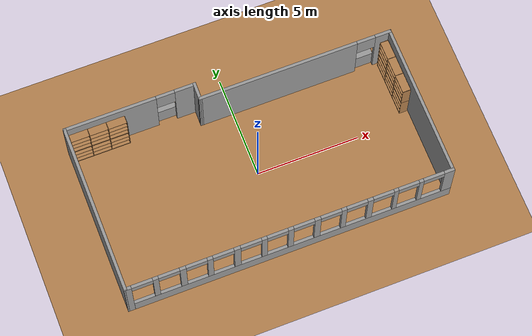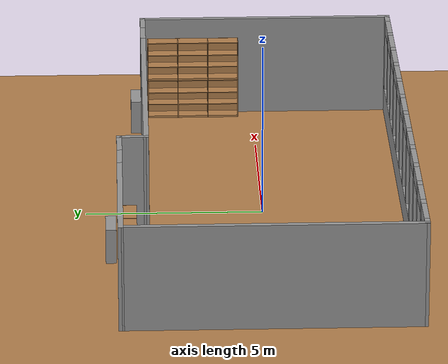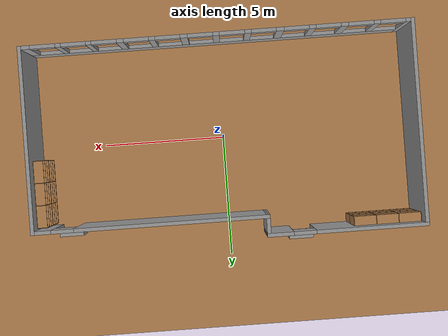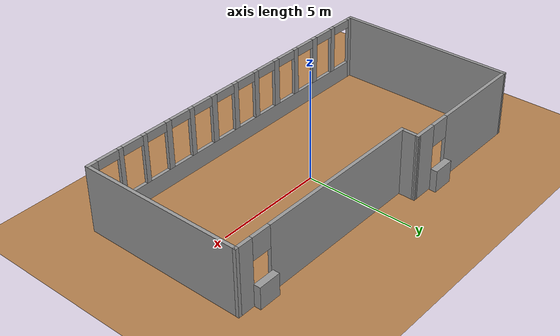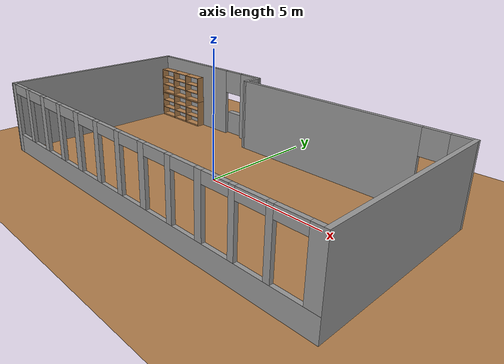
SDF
<sdf version="1.6">
 <world name="default">
  <light name="sun" type="directional">
   <pose>0 0 10 0 -0 0</pose>
   <diffuse>0.8 0.8 0.8 1</diffuse>
   <specular>0.2 0.2 0.2 1</specular>
   <attenuation>
    <range>1000</range>
    <constant>0.9</constant>
    <linear>0.01</linear>
    <quadratic>0.001</quadratic>
   </attenuation>
   <direction>-0.5 0.1 -0.9</direction>
  </light>
  <physics type="ode">
   <real_time_update_rate>50.0</real_time_update_rate>
   <max_step_size>0.02</max_step_size>
   <real_time_factor>0</real_time_factor>
   <ode>
    <solver>
     <type>quick</type>
     <iters>1000</iters>
     <precon_iters>0</precon_iters>
     <sor>1.200000</sor>
     <use_dynamic_moi_rescaling>1</use_dynamic_moi_rescaling>
    </solver>
    <constraints>
     <cfm>0.00001</cfm>
     <erp>0.2</erp>
     <contact_max_correcting_vel>2000.000000</contact_max_correcting_vel>
     <contact_surface_layer>0.01000</contact_surface_layer>
    </constraints>
   </ode>
  </physics>
  <gravity>0 0 -9.8</gravity>
  <scene><ambient>0.4 0.4 0.4 1</ambient><background>0.7 0.7 0.7 1</background><shadows>0</shadows></scene>
  <magnetic_field>6e-06 2.3e-05 -4.2e-05</magnetic_field>
  <atmosphere type="adiabatic"/>
  <audio><device>default</device></audio>
  <spherical_coordinates>
   <surface_model>EARTH_WGS84</surface_model>
   <latitude_deg>0</latitude_deg>
   <longitude_deg>0</longitude_deg>
   <elevation>0</elevation>
   <heading_deg>0</heading_deg>
  </spherical_coordinates>
  <model name="lab_empty">
   <link name="Wall_10">
    <pose>-4.66996 4.04955 0 0 -0 0</pose>
    <visual name="Wall_10_Visual_0">
     <pose>-0.979064 0 1.5 0 -0 0</pose>
     <geometry><box><size>4.46087 0.15 3</size></box></geometry>
     <material>
      <script><uri>file://media/materials/scripts/gazebo.material</uri><name>Gazebo/Grey</name></script>
      <ambient>0.95 0.95 0.95 1</ambient>
     </material>
     <meta><layer>0</layer></meta>
    </visual>
    <collision name="Wall_10_Collision_0">
     <geometry><box><size>4.46087 0.15 3</size></box></geometry>
     <pose>-0.979064 0 1.5 0 -0 0</pose>
    </collision>
    <visual name="Wall_10_Visual_1">
     <pose>2.68044 0 1.5 0 -0 0</pose>
     <geometry><box><size>1.05813 0.15 3</size></box></geometry>
     <material>
      <script><uri>file://media/materials/scripts/gazebo.material</uri><name>Gazebo/Grey</name></script>
      <ambient>0.95 0.95 0.95 1</ambient>
     </material>
     <meta><layer>0</layer></meta>
    </visual>
    <collision name="Wall_10_Collision_1">
     <geometry><box><size>1.05813 0.15 3</size></box></geometry>
     <pose>2.68044 0 1.5 0 -0 0</pose>
    </collision>
    <visual name="Wall_10_Visual_2">
     <pose>1.70137 0 2.5 0 -0 0</pose>
     <geometry><box><size>0.9 0.15 1</size></box></geometry>
     <material>
      <script><uri>file://media/materials/scripts/gazebo.material</uri><name>Gazebo/Grey</name></script>
      <ambient>0.95 0.95 0.95 1</ambient>
     </material>
     <meta><layer>0</layer></meta>
    </visual>
    <collision name="Wall_10_Collision_2">
     <geometry><box><size>0.9 0.15 1</size></box></geometry>
     <pose>1.70137 0 2.5 0 -0 0</pose>
    </collision>
   </link>
   <link name="Wall_13">
    <collision name="Wall_13_Collision">
     <geometry><box><size>0.900067 0.15 3</size></box></geometry>
     <pose>0 0 1.5 0 -0 0</pose>
    </collision>
    <visual name="Wall_13_Visual">
     <pose>0 0 1.5 0 -0 0</pose>
     <geometry><box><size>0.900067 0.15 3</size></box></geometry>
     <material>
      <script><uri>file://media/materials/scripts/gazebo.material</uri><name>Gazebo/Grey</name></script>
      <ambient>1 1 1 1</ambient>
     </material>
     <meta><layer>0</layer></meta>
    </visual>
    <pose>-1.54046 3.67455 0 0 -0 -1.58413</pose>
   </link>
   <link name="Wall_15">
    <pose>0.004542 -4.05046 0 0 -0 0</pose>
    <visual name="Wall_15_Visual_0">
     <pose>-7.70321 0 1.5 0 -0 0</pose>
     <geometry><box><size>0.343585 0.15 3</size></box></geometry>
     <material>
      <script><uri>file://media/materials/scripts/gazebo.material</uri><name>Gazebo/Grey</name></script>
      <ambient>0.2 0.2 0.2 1</ambient>
     </material>
     <meta><layer>0</layer></meta>
    </visual>
    <collision name="Wall_15_Collision_0">
     <geometry><box><size>0.343585 0.15 3</size></box></geometry>
     <pose>-7.70321 0 1.5 0 -0 0</pose>
    </collision>
    <visual name="Wall_15_Visual_1">
     <pose>0.171792 0 0.4 0 -0 0</pose>
     <geometry><box><size>15.4064 0.15 0.8</size></box></geometry>
     <material>
      <script><uri>file://media/materials/scripts/gazebo.material</uri><name>Gazebo/Grey</name></script>
      <ambient>0.2 0.2 0.2 1</ambient>
     </material>
     <meta><layer>0</layer></meta>
    </visual>
    <collision name="Wall_15_Collision_1">
     <geometry><box><size>15.4064 0.15 0.8</size></box></geometry>
     <pose>0.171792 0 0.4 0 -0 0</pose>
    </collision>
    <visual name="Wall_15_Visual_2">
     <pose>-6.39989 0 1.9 0 -0 0</pose>
     <geometry><box><size>0.263044 0.15 2.2</size></box></geometry>
     <material>
      <script><uri>file://media/materials/scripts/gazebo.material</uri><name>Gazebo/Grey</name></script>
      <ambient>0.2 0.2 0.2 1</ambient>
     </material>
     <meta><layer>0</layer></meta>
    </visual>
    <collision name="Wall_15_Collision_2">
     <geometry><box><size>0.263044 0.15 2.2</size></box></geometry>
     <pose>-6.39989 0 1.9 0 -0 0</pose>
    </collision>
    <visual name="Wall_15_Visual_3">
     <pose>-5.12163 0 1.9 0 -0 0</pose>
     <geometry><box><size>0.293478 0.15 2.2</size></box></geometry>
     <material>
      <script><uri>file://media/materials/scripts/gazebo.material</uri><name>Gazebo/Grey</name></script>
      <ambient>0.2 0.2 0.2 1</ambient>
     </material>
     <meta><layer>0</layer></meta>
    </visual>
    <collision name="Wall_15_Collision_3">
     <geometry><box><size>0.293478 0.15 2.2</size></box></geometry>
     <pose>-5.12163 0 1.9 0 -0 0</pose>
    </collision>
    <visual name="Wall_15_Visual_4">
     <pose>-3.84337 0 1.9 0 -0 0</pose>
     <geometry><box><size>0.263043 0.15 2.2</size></box></geometry>
     <material>
      <script><uri>file://media/materials/scripts/gazebo.material</uri><name>Gazebo/Grey</name></script>
      <ambient>0.2 0.2 0.2 1</ambient>
     </material>
     <meta><layer>0</layer></meta>
    </visual>
    <collision name="Wall_15_Collision_4">
     <geometry><box><size>0.263043 0.15 2.2</size></box></geometry>
     <pose>-3.84337 0 1.9 0 -0 0</pose>
    </collision>
    <visual name="Wall_15_Visual_5">
     <pose>-2.5575 0 1.9 0 -0 0</pose>
     <geometry><box><size>0.308696 0.15 2.2</size></box></geometry>
     <material>
      <script><uri>file://media/materials/scripts/gazebo.material</uri><name>Gazebo/Grey</name></script>
      <ambient>0.2 0.2 0.2 1</ambient>
     </material>
     <meta><layer>0</layer></meta>
    </visual>
    <collision name="Wall_15_Collision_5">
     <geometry><box><size>0.308696 0.15 2.2</size></box></geometry>
     <pose>-2.5575 0 1.9 0 -0 0</pose>
    </collision>
    <visual name="Wall_15_Visual_6">
     <pose>-1.27163 0 1.9 0 -0 0</pose>
     <geometry><box><size>0.263044 0.15 2.2</size></box></geometry>
     <material>
      <script><uri>file://media/materials/scripts/gazebo.material</uri><name>Gazebo/Grey</name></script>
      <ambient>0.2 0.2 0.2 1</ambient>
     </material>
     <meta><layer>0</layer></meta>
    </visual>
    <collision name="Wall_15_Collision_6">
     <geometry><box><size>0.263044 0.15 2.2</size></box></geometry>
     <pose>-1.27163 0 1.9 0 -0 0</pose>
    </collision>
    <visual name="Wall_15_Visual_7">
     <pose>-0.008589 0 1.9 0 -0 0</pose>
     <geometry><box><size>0.263043 0.15 2.2</size></box></geometry>
     <material>
      <script><uri>file://media/materials/scripts/gazebo.material</uri><name>Gazebo/Grey</name></script>
      <ambient>0.2 0.2 0.2 1</ambient>
     </material>
     <meta><layer>0</layer></meta>
    </visual>
    <collision name="Wall_15_Collision_7">
     <geometry><box><size>0.263043 0.15 2.2</size></box></geometry>
     <pose>-0.008589 0 1.9 0 -0 0</pose>
    </collision>
    <visual name="Wall_15_Visual_8">
     <pose>1.26967 0 1.9 0 -0 0</pose>
     <geometry><box><size>0.293478 0.15 2.2</size></box></geometry>
     <material>
      <script><uri>file://media/materials/scripts/gazebo.material</uri><name>Gazebo/Grey</name></script>
      <ambient>0.2 0.2 0.2 1</ambient>
     </material>
     <meta><layer>0</layer></meta>
    </visual>
    <collision name="Wall_15_Collision_8">
     <geometry><box><size>0.293478 0.15 2.2</size></box></geometry>
     <pose>1.26967 0 1.9 0 -0 0</pose>
    </collision>
    <visual name="Wall_15_Visual_9">
     <pose>2.54032 0 1.9 0 -0 0</pose>
     <geometry><box><size>0.247826 0.15 2.2</size></box></geometry>
     <material>
      <script><uri>file://media/materials/scripts/gazebo.material</uri><name>Gazebo/Grey</name></script>
      <ambient>0.2 0.2 0.2 1</ambient>
     </material>
     <meta><layer>0</layer></meta>
    </visual>
    <collision name="Wall_15_Collision_9">
     <geometry><box><size>0.247826 0.15 2.2</size></box></geometry>
     <pose>2.54032 0 1.9 0 -0 0</pose>
    </collision>
    <visual name="Wall_15_Visual_10">
     <pose>3.80337 0 1.9 0 -0 0</pose>
     <geometry><box><size>0.278261 0.15 2.2</size></box></geometry>
     <material>
      <script><uri>file://media/materials/scripts/gazebo.material</uri><name>Gazebo/Grey</name></script>
      <ambient>0.2 0.2 0.2 1</ambient>
     </material>
     <meta><layer>0</layer></meta>
    </visual>
    <collision name="Wall_15_Collision_10">
     <geometry><box><size>0.278261 0.15 2.2</size></box></geometry>
     <pose>3.80337 0 1.9 0 -0 0</pose>
    </collision>
    <visual name="Wall_15_Visual_11">
     <pose>5.05119 0 1.9 0 -0 0</pose>
     <geometry><box><size>0.217391 0.15 2.2</size></box></geometry>
     <material>
      <script><uri>file://media/materials/scripts/gazebo.material</uri><name>Gazebo/Grey</name></script>
      <ambient>0.2 0.2 0.2 1</ambient>
     </material>
     <meta><layer>0</layer></meta>
    </visual>
    <collision name="Wall_15_Collision_11">
     <geometry><box><size>0.217391 0.15 2.2</size></box></geometry>
     <pose>5.05119 0 1.9 0 -0 0</pose>
    </collision>
    <visual name="Wall_15_Visual_12">
     <pose>6.26858 0 1.9 0 -0 0</pose>
     <geometry><box><size>0.217391 0.15 2.2</size></box></geometry>
     <material>
      <script><uri>file://media/materials/scripts/gazebo.material</uri><name>Gazebo/Grey</name></script>
      <ambient>0.2 0.2 0.2 1</ambient>
     </material>
     <meta><layer>0</layer></meta>
    </visual>
    <collision name="Wall_15_Collision_12">
     <geometry><box><size>0.217391 0.15 2.2</size></box></geometry>
     <pose>6.26858 0 1.9 0 -0 0</pose>
    </collision>
    <visual name="Wall_15_Visual_13">
     <pose>7.62614 0 1.9 0 -0 0</pose>
     <geometry><box><size>0.497719 0.15 2.2</size></box></geometry>
     <material>
      <script><uri>file://media/materials/scripts/gazebo.material</uri><name>Gazebo/Grey</name></script>
      <ambient>0.2 0.2 0.2 1</ambient>
     </material>
     <meta><layer>0</layer></meta>
    </visual>
    <collision name="Wall_15_Collision_13">
     <geometry><box><size>0.497719 0.15 2.2</size></box></geometry>
     <pose>7.62614 0 1.9 0 -0 0</pose>
    </collision>
    <visual name="Wall_15_Visual_14">
     <pose>-7.03141 0 2.8 0 -0 0</pose>
     <geometry><box><size>1 0.15 0.4</size></box></geometry>
     <material>
      <script><uri>file://media/materials/scripts/gazebo.material</uri><name>Gazebo/Grey</name></script>
      <ambient>0.2 0.2 0.2 1</ambient>
     </material>
     <meta><layer>0</layer></meta>
    </visual>
    <collision name="Wall_15_Collision_14">
     <geometry><box><size>1 0.15 0.4</size></box></geometry>
     <pose>-7.03141 0 2.8 0 -0 0</pose>
    </collision>
    <visual name="Wall_15_Visual_15">
     <pose>-5.76837 0 2.8 0 -0 0</pose>
     <geometry><box><size>1 0.15 0.4</size></box></geometry>
     <material>
      <script><uri>file://media/materials/scripts/gazebo.material</uri><name>Gazebo/Grey</name></script>
      <ambient>0.2 0.2 0.2 1</ambient>
     </material>
     <meta><layer>0</layer></meta>
    </visual>
    <collision name="Wall_15_Collision_15">
     <geometry><box><size>1 0.15 0.4</size></box></geometry>
     <pose>-5.76837 0 2.8 0 -0 0</pose>
    </collision>
    <visual name="Wall_15_Visual_16">
     <pose>-4.47489 0 2.8 0 -0 0</pose>
     <geometry><box><size>1 0.15 0.4</size></box></geometry>
     <material>
      <script><uri>file://media/materials/scripts/gazebo.material</uri><name>Gazebo/Grey</name></script>
      <ambient>0.2 0.2 0.2 1</ambient>
     </material>
     <meta><layer>0</layer></meta>
    </visual>
    <collision name="Wall_15_Collision_16">
     <geometry><box><size>1 0.15 0.4</size></box></geometry>
     <pose>-4.47489 0 2.8 0 -0 0</pose>
    </collision>
    <visual name="Wall_15_Visual_17">
     <pose>-3.21185 0 2.8 0 -0 0</pose>
     <geometry><box><size>1 0.15 0.4</size></box></geometry>
     <material>
      <script><uri>file://media/materials/scripts/gazebo.material</uri><name>Gazebo/Grey</name></script>
      <ambient>0.2 0.2 0.2 1</ambient>
     </material>
     <meta><layer>0</layer></meta>
    </visual>
    <collision name="Wall_15_Collision_17">
     <geometry><box><size>1 0.15 0.4</size></box></geometry>
     <pose>-3.21185 0 2.8 0 -0 0</pose>
    </collision>
    <visual name="Wall_15_Visual_18">
     <pose>-1.90315 0 2.8 0 -0 0</pose>
     <geometry><box><size>1 0.15 0.4</size></box></geometry>
     <material>
      <script><uri>file://media/materials/scripts/gazebo.material</uri><name>Gazebo/Grey</name></script>
      <ambient>0.2 0.2 0.2 1</ambient>
     </material>
     <meta><layer>0</layer></meta>
    </visual>
    <collision name="Wall_15_Collision_18">
     <geometry><box><size>1 0.15 0.4</size></box></geometry>
     <pose>-1.90315 0 2.8 0 -0 0</pose>
    </collision>
    <visual name="Wall_15_Visual_19">
     <pose>-0.640111 0 2.8 0 -0 0</pose>
     <geometry><box><size>1 0.15 0.4</size></box></geometry>
     <material>
      <script><uri>file://media/materials/scripts/gazebo.material</uri><name>Gazebo/Grey</name></script>
      <ambient>0.2 0.2 0.2 1</ambient>
     </material>
     <meta><layer>0</layer></meta>
    </visual>
    <collision name="Wall_15_Collision_19">
     <geometry><box><size>1 0.15 0.4</size></box></geometry>
     <pose>-0.640111 0 2.8 0 -0 0</pose>
    </collision>
    <visual name="Wall_15_Visual_20">
     <pose>0.622933 0 2.8 0 -0 0</pose>
     <geometry><box><size>1 0.15 0.4</size></box></geometry>
     <material>
      <script><uri>file://media/materials/scripts/gazebo.material</uri><name>Gazebo/Grey</name></script>
      <ambient>0.2 0.2 0.2 1</ambient>
     </material>
     <meta><layer>0</layer></meta>
    </visual>
    <collision name="Wall_15_Collision_20">
     <geometry><box><size>1 0.15 0.4</size></box></geometry>
     <pose>0.622933 0 2.8 0 -0 0</pose>
    </collision>
    <visual name="Wall_15_Visual_21">
     <pose>1.91641 0 2.8 0 -0 0</pose>
     <geometry><box><size>1 0.15 0.4</size></box></geometry>
     <material>
      <script><uri>file://media/materials/scripts/gazebo.material</uri><name>Gazebo/Grey</name></script>
      <ambient>0.2 0.2 0.2 1</ambient>
     </material>
     <meta><layer>0</layer></meta>
    </visual>
    <collision name="Wall_15_Collision_21">
     <geometry><box><size>1 0.15 0.4</size></box></geometry>
     <pose>1.91641 0 2.8 0 -0 0</pose>
    </collision>
    <visual name="Wall_15_Visual_22">
     <pose>3.16424 0 2.8 0 -0 0</pose>
     <geometry><box><size>1 0.15 0.4</size></box></geometry>
     <material>
      <script><uri>file://media/materials/scripts/gazebo.material</uri><name>Gazebo/Grey</name></script>
      <ambient>0.2 0.2 0.2 1</ambient>
     </material>
     <meta><layer>0</layer></meta>
    </visual>
    <collision name="Wall_15_Collision_22">
     <geometry><box><size>1 0.15 0.4</size></box></geometry>
     <pose>3.16424 0 2.8 0 -0 0</pose>
    </collision>
    <visual name="Wall_15_Visual_23">
     <pose>4.4425 0 2.8 0 -0 0</pose>
     <geometry><box><size>1 0.15 0.4</size></box></geometry>
     <material>
      <script><uri>file://media/materials/scripts/gazebo.material</uri><name>Gazebo/Grey</name></script>
      <ambient>0.2 0.2 0.2 1</ambient>
     </material>
     <meta><layer>0</layer></meta>
    </visual>
    <collision name="Wall_15_Collision_23">
     <geometry><box><size>1 0.15 0.4</size></box></geometry>
     <pose>4.4425 0 2.8 0 -0 0</pose>
    </collision>
    <visual name="Wall_15_Visual_24">
     <pose>5.65989 0 2.8 0 -0 0</pose>
     <geometry><box><size>1 0.15 0.4</size></box></geometry>
     <material>
      <script><uri>file://media/materials/scripts/gazebo.material</uri><name>Gazebo/Grey</name></script>
      <ambient>0.2 0.2 0.2 1</ambient>
     </material>
     <meta><layer>0</layer></meta>
    </visual>
    <collision name="Wall_15_Collision_24">
     <geometry><box><size>1 0.15 0.4</size></box></geometry>
     <pose>5.65989 0 2.8 0 -0 0</pose>
    </collision>
    <visual name="Wall_15_Visual_25">
     <pose>6.87728 0 2.8 0 -0 0</pose>
     <geometry><box><size>1 0.15 0.4</size></box></geometry>
     <material>
      <script><uri>file://media/materials/scripts/gazebo.material</uri><name>Gazebo/Grey</name></script>
      <ambient>0.2 0.2 0.2 1</ambient>
     </material>
     <meta><layer>0</layer></meta>
    </visual>
    <collision name="Wall_15_Collision_25">
     <geometry><box><size>1 0.15 0.4</size></box></geometry>
     <pose>6.87728 0 2.8 0 -0 0</pose>
    </collision>
   </link>
   <link name="Wall_17">
    <collision name="Wall_17_Collision">
     <geometry><box><size>8.25 0.15 3</size></box></geometry>
     <pose>0 0 1.5 0 -0 0</pose>
    </collision>
    <visual name="Wall_17_Visual">
     <pose>0 0 1.5 0 -0 0</pose>
     <geometry><box><size>8.25 0.15 3</size></box></geometry>
     <material>
      <script><uri>file://media/materials/scripts/gazebo.material</uri><name>Gazebo/Grey</name></script>
      <ambient>0.95 0.95 0.95 1</ambient>
     </material>
     <meta><layer>0</layer></meta>
    </visual>
    <pose>-7.79996 -0.000455 0 0 -0 -1.56968</pose>
   </link>
   <link name="Wall_2">
    <collision name="Wall_2_Collision">
     <geometry><box><size>7.5 0.15 3</size></box></geometry>
     <pose>0 0 1.5 0 -0 0</pose>
    </collision>
    <visual name="Wall_2_Visual">
     <pose>0 0 1.5 0 -0 0</pose>
     <geometry><box><size>7.5 0.15 3</size></box></geometry>
     <material>
      <script><uri>file://media/materials/scripts/gazebo.material</uri><name>Gazebo/Grey</name></script>
      <ambient>0.95 0.95 0.95 1</ambient>
     </material>
     <meta><layer>0</layer></meta>
    </visual>
    <pose>7.80454 -0.375455 0 0 -0 1.5708</pose>
   </link>
   <link name="Wall_3">
    <pose>3.12954 3.29955 0 0 -0 3.14159</pose>
    <visual name="Wall_3_Visual_0">
     <pose>-4.346 0 1.5 0 -0 0</pose>
     <geometry><box><size>0.808 0.15 3</size></box></geometry>
     <material>
      <script><uri>file://media/materials/scripts/gazebo.material</uri><name>Gazebo/Grey</name></script>
      <ambient>0.95 0.95 0.95 1</ambient>
     </material>
     <meta><layer>0</layer></meta>
    </visual>
    <collision name="Wall_3_Collision_0">
     <geometry><box><size>0.808 0.15 3</size></box></geometry>
     <pose>-4.346 0 1.5 0 -0 0</pose>
    </collision>
    <visual name="Wall_3_Visual_1">
     <pose>0.854 0 1.5 0 -0 0</pose>
     <geometry><box><size>7.792 0.15 3</size></box></geometry>
     <material>
      <script><uri>file://media/materials/scripts/gazebo.material</uri><name>Gazebo/Grey</name></script>
      <ambient>0.95 0.95 0.95 1</ambient>
     </material>
     <meta><layer>0</layer></meta>
    </visual>
    <collision name="Wall_3_Collision_1">
     <geometry><box><size>7.792 0.15 3</size></box></geometry>
     <pose>0.854 0 1.5 0 -0 0</pose>
    </collision>
    <visual name="Wall_3_Visual_2">
     <pose>-3.492 0 2.5 0 -0 0</pose>
     <geometry><box><size>0.9 0.15 1</size></box></geometry>
     <material>
      <script><uri>file://media/materials/scripts/gazebo.material</uri><name>Gazebo/Grey</name></script>
      <ambient>0.95 0.95 0.95 1</ambient>
     </material>
     <meta><layer>0</layer></meta>
    </visual>
    <collision name="Wall_3_Collision_2">
     <geometry><box><size>0.9 0.15 1</size></box></geometry>
     <pose>-3.492 0 2.5 0 -0 0</pose>
    </collision>
   </link>
   <static>1</static>
  </model>
  <model name="ground_plane">
   <static>1</static>
   <link name="link">
    <collision name="collision">
     <geometry><plane><normal>0 0 1</normal><size>16 9</size></plane></geometry>
     <surface>
      <contact><collide_bitmask>65535</collide_bitmask></contact>
      <friction><ode><mu>100</mu><mu2>50</mu2></ode></friction>
     </surface>
    </collision>
    <visual name="visual">
     <cast_shadows>0</cast_shadows>
     <geometry><plane><normal>0 0 1</normal><size>16 8</size></plane></geometry>
     <material>
      <script><uri>file://media/materials/scripts/gazebo.material</uri><name>Gazebo/Wood</name></script>
     </material>
    </visual>
   </link>
  </model>
  <model name="unit_box">
   <link name="link">
    <inertial>
     <mass>0.300562</mass>
     <inertia>
      <ixx>0.0273083</ixx>
      <ixy>0</ixy>
      <ixz>0</ixz>
      <iyy>0.0500937</iyy>
      <iyz>0</iyz>
      <izz>0.0273083</izz>
     </inertia>
    </inertial>
    <pose>-0 -0.356332 0 0 -0 0</pose>
    <visual name="visual">
     <geometry><box><size>1 0.30048 1</size></box></geometry>
     <material>
      <script><name>Gazebo/Grey</name><uri>file://media/materials/scripts/gazebo.material</uri></script>
     </material>
    </visual>
    <collision name="collision">
     <geometry><box><size>1 0.30048 1</size></box></geometry>
     <surface>
      <friction>
       <ode><mu>1</mu><mu2>1</mu2><fdir1>0 0 0</fdir1><slip1>0</slip1><slip2>0</slip2></ode>
       <torsional>
        <coefficient>1</coefficient>
        <patch_radius>0</patch_radius>
        <surface_radius>0</surface_radius>
        <use_patch_radius>1</use_patch_radius>
        <ode><slip>0</slip></ode>
       </torsional>
      </friction>
      <bounce><restitution_coefficient>0</restitution_coefficient><threshold>1e+06</threshold></bounce>
      <contact>
       <collide_without_contact>0</collide_without_contact>
       <collide_without_contact_bitmask>1</collide_without_contact_bitmask>
       <collide_bitmask>1</collide_bitmask>
       <ode>
        <soft_cfm>0</soft_cfm>
        <soft_erp>0.2</soft_erp>
        <kp>1e+13</kp>
        <kd>1</kd>
        <max_vel>0.01</max_vel>
        <min_depth>0</min_depth>
       </ode>
       <bullet>
        <split_impulse>1</split_impulse>
        <split_impulse_penetration_threshold>-0.01</split_impulse_penetration_threshold>
        <soft_cfm>0</soft_cfm>
        <soft_erp>0.2</soft_erp>
        <kp>1e+13</kp>
        <kd>1</kd>
       </bullet>
      </contact>
     </surface>
    </collision>
   </link>
   <static>1</static>
   <pose>-2.96131 4.66258 0.5 0 -0 0</pose>
  </model>
  <model name="unit_box_clone">
   <link name="link">
    <inertial>
     <mass>0.300562</mass>
     <inertia>
      <ixx>0.0273083</ixx>
      <ixy>0</ixy>
      <ixz>0</ixz>
      <iyy>0.0500937</iyy>
      <iyz>0</iyz>
      <izz>0.0273083</izz>
     </inertia>
    </inertial>
    <pose>-0 -0.356332 0 0 -0 0</pose>
    <visual name="visual">
     <geometry><box><size>1 0.30048 1</size></box></geometry>
     <material>
      <script><name>Gazebo/Grey</name><uri>file://media/materials/scripts/gazebo.material</uri></script>
     </material>
    </visual>
    <collision name="collision">
     <geometry><box><size>1 0.30048 1</size></box></geometry>
     <surface>
      <friction>
       <ode><mu>1</mu><mu2>1</mu2><fdir1>0 0 0</fdir1><slip1>0</slip1><slip2>0</slip2></ode>
       <torsional>
        <coefficient>1</coefficient>
        <patch_radius>0</patch_radius>
        <surface_radius>0</surface_radius>
        <use_patch_radius>1</use_patch_radius>
        <ode><slip>0</slip></ode>
       </torsional>
      </friction>
      <bounce><restitution_coefficient>0</restitution_coefficient><threshold>1e+06</threshold></bounce>
      <contact>
       <collide_without_contact>0</collide_without_contact>
       <collide_without_contact_bitmask>1</collide_without_contact_bitmask>
       <collide_bitmask>1</collide_bitmask>
       <ode>
        <soft_cfm>0</soft_cfm>
        <soft_erp>0.2</soft_erp>
        <kp>1e+13</kp>
        <kd>1</kd>
        <max_vel>0.01</max_vel>
        <min_depth>0</min_depth>
       </ode>
       <bullet>
        <split_impulse>1</split_impulse>
        <split_impulse_penetration_threshold>-0.01</split_impulse_penetration_threshold>
        <soft_cfm>0</soft_cfm>
        <soft_erp>0.2</soft_erp>
        <kp>1e+13</kp>
        <kd>1</kd>
       </bullet>
      </contact>
     </surface>
    </collision>
   </link>
   <static>1</static>
   <pose>6.59551 3.88207 0.5 0 -0 0</pose>
  </model>
  <model name="Bookshelf">
   <static>1</static>
   <link name="link">
    <inertial><mass>1</mass></inertial>
    <collision name="back">
     <pose>0 0.005 0.6 0 -0 0</pose>
     <geometry><box><size>0.9 0.01 1.2</size></box></geometry>
    </collision>
    <visual name="visual1">
     <pose>0 0.005 0.6 0 -0 0</pose>
     <geometry><box><size>0.9 0.01 1.2</size></box></geometry>
     <material>
      <diffuse>1 1 1 1</diffuse>
      <script><uri>file://media/materials/scripts/gazebo.material</uri><name>Gazebo/Wood</name></script>
     </material>
    </visual>
    <collision name="left_side">
     <pose>0.45 -0.195 0.6 0 -0 0</pose>
     <geometry><box><size>0.02 0.4 1.2</size></box></geometry>
    </collision>
    <visual name="visual2">
     <pose>0.45 -0.195 0.6 0 -0 0</pose>
     <geometry><box><size>0.02 0.4 1.2</size></box></geometry>
     <material>
      <diffuse>1 1 1 1</diffuse>
      <script><uri>file://media/materials/scripts/gazebo.material</uri><name>Gazebo/Wood</name></script>
     </material>
    </visual>
    <collision name="right_side">
     <pose>-0.45 -0.195 0.6 0 -0 0</pose>
     <geometry><box><size>0.02 0.4 1.2</size></box></geometry>
    </collision>
    <visual name="visual3">
     <pose>-0.45 -0.195 0.6 0 -0 0</pose>
     <geometry><box><size>0.02 0.4 1.2</size></box></geometry>
     <material>
      <diffuse>1 1 1 1</diffuse>
      <script><uri>file://media/materials/scripts/gazebo.material</uri><name>Gazebo/Wood</name></script>
     </material>
    </visual>
    <collision name="bottom">
     <pose>0 -0.195 0.03 0 -0 0</pose>
     <geometry><box><size>0.88 0.4 0.06</size></box></geometry>
    </collision>
    <visual name="visual4">
     <pose>0 -0.195 0.03 0 -0 0</pose>
     <geometry><box><size>0.88 0.4 0.06</size></box></geometry>
     <material>
      <diffuse>1 1 1 1</diffuse>
      <script><uri>file://media/materials/scripts/gazebo.material</uri><name>Gazebo/Wood</name></script>
     </material>
    </visual>
    <collision name="top">
     <pose>0 -0.195 1.19 0 -0 0</pose>
     <geometry><box><size>0.88 0.4 0.02</size></box></geometry>
    </collision>
    <visual name="visual5">
     <pose>0 -0.195 1.19 0 -0 0</pose>
     <geometry><box><size>0.88 0.4 0.02</size></box></geometry>
     <material>
      <diffuse>1 1 1 1</diffuse>
      <script><uri>file://media/materials/scripts/gazebo.material</uri><name>Gazebo/Wood</name></script>
     </material>
    </visual>
    <collision name="low_shelf">
     <pose>0 -0.195 0.43 0 -0 0</pose>
     <geometry><box><size>0.88 0.4 0.02</size></box></geometry>
    </collision>
    <visual name="visual6">
     <pose>0 -0.195 0.43 0 -0 0</pose>
     <geometry><box><size>0.88 0.4 0.02</size></box></geometry>
     <material>
      <diffuse>1 1 1 1</diffuse>
      <script><uri>file://media/materials/scripts/gazebo.material</uri><name>Gazebo/Wood</name></script>
     </material>
    </visual>
    <collision name="high_shelf">
     <pose>0 -0.195 0.8 0 -0 0</pose>
     <geometry><box><size>0.88 0.4 0.02</size></box></geometry>
    </collision>
    <visual name="visual7">
     <pose>0 -0.195 0.8 0 -0 0</pose>
     <geometry><box><size>0.88 0.4 0.02</size></box></geometry>
     <material>
      <diffuse>1 1 1 1</diffuse>
      <script><uri>file://media/materials/scripts/gazebo.material</uri><name>Gazebo/Wood</name></script>
     </material>
    </visual>
   </link>
   <pose>-7.25 4 0 0 -0 0</pose>
  </model>
  <model name="Bookshelf_clone">
   <static>1</static>
   <link name="link">
    <inertial><mass>1</mass></inertial>
    <collision name="back">
     <pose>0 0.005 0.6 0 -0 0</pose>
     <geometry><box><size>0.9 0.01 1.2</size></box></geometry>
    </collision>
    <visual name="visual1">
     <pose>0 0.005 0.6 0 -0 0</pose>
     <geometry><box><size>0.9 0.01 1.2</size></box></geometry>
     <material>
      <diffuse>1 1 1 1</diffuse>
      <script><uri>file://media/materials/scripts/gazebo.material</uri><name>Gazebo/Wood</name></script>
     </material>
    </visual>
    <collision name="left_side">
     <pose>0.45 -0.195 0.6 0 -0 0</pose>
     <geometry><box><size>0.02 0.4 1.2</size></box></geometry>
    </collision>
    <visual name="visual2">
     <pose>0.45 -0.195 0.6 0 -0 0</pose>
     <geometry><box><size>0.02 0.4 1.2</size></box></geometry>
     <material>
      <diffuse>1 1 1 1</diffuse>
      <script><uri>file://media/materials/scripts/gazebo.material</uri><name>Gazebo/Wood</name></script>
     </material>
    </visual>
    <collision name="right_side">
     <pose>-0.45 -0.195 0.6 0 -0 0</pose>
     <geometry><box><size>0.02 0.4 1.2</size></box></geometry>
    </collision>
    <visual name="visual3">
     <pose>-0.45 -0.195 0.6 0 -0 0</pose>
     <geometry><box><size>0.02 0.4 1.2</size></box></geometry>
     <material>
      <diffuse>1 1 1 1</diffuse>
      <script><uri>file://media/materials/scripts/gazebo.material</uri><name>Gazebo/Wood</name></script>
     </material>
    </visual>
    <collision name="bottom">
     <pose>0 -0.195 0.03 0 -0 0</pose>
     <geometry><box><size>0.88 0.4 0.06</size></box></geometry>
    </collision>
    <visual name="visual4">
     <pose>0 -0.195 0.03 0 -0 0</pose>
     <geometry><box><size>0.88 0.4 0.06</size></box></geometry>
     <material>
      <diffuse>1 1 1 1</diffuse>
      <script><uri>file://media/materials/scripts/gazebo.material</uri><name>Gazebo/Wood</name></script>
     </material>
    </visual>
    <collision name="top">
     <pose>0 -0.195 1.19 0 -0 0</pose>
     <geometry><box><size>0.88 0.4 0.02</size></box></geometry>
    </collision>
    <visual name="visual5">
     <pose>0 -0.195 1.19 0 -0 0</pose>
     <geometry><box><size>0.88 0.4 0.02</size></box></geometry>
     <material>
      <diffuse>1 1 1 1</diffuse>
      <script><uri>file://media/materials/scripts/gazebo.material</uri><name>Gazebo/Wood</name></script>
     </material>
    </visual>
    <collision name="low_shelf">
     <pose>0 -0.195 0.43 0 -0 0</pose>
     <geometry><box><size>0.88 0.4 0.02</size></box></geometry>
    </collision>
    <visual name="visual6">
     <pose>0 -0.195 0.43 0 -0 0</pose>
     <geometry><box><size>0.88 0.4 0.02</size></box></geometry>
     <material>
      <diffuse>1 1 1 1</diffuse>
      <script><uri>file://media/materials/scripts/gazebo.material</uri><name>Gazebo/Wood</name></script>
     </material>
    </visual>
    <collision name="high_shelf">
     <pose>0 -0.195 0.8 0 -0 0</pose>
     <geometry><box><size>0.88 0.4 0.02</size></box></geometry>
    </collision>
    <visual name="visual7">
     <pose>0 -0.195 0.8 0 -0 0</pose>
     <geometry><box><size>0.88 0.4 0.02</size></box></geometry>
     <material>
      <diffuse>1 1 1 1</diffuse>
      <script><uri>file://media/materials/scripts/gazebo.material</uri><name>Gazebo/Wood</name></script>
     </material>
    </visual>
   </link>
   <pose>-6.35 4 0 0 -0 0</pose>
  </model>
  <model name="Bookshelf_clone_0">
   <static>1</static>
   <link name="link">
    <inertial><mass>1</mass></inertial>
    <collision name="back">
     <pose>0 0.005 0.6 0 -0 0</pose>
     <geometry><box><size>0.9 0.01 1.2</size></box></geometry>
    </collision>
    <visual name="visual1">
     <pose>0 0.005 0.6 0 -0 0</pose>
     <geometry><box><size>0.9 0.01 1.2</size></box></geometry>
     <material>
      <diffuse>1 1 1 1</diffuse>
      <script><uri>file://media/materials/scripts/gazebo.material</uri><name>Gazebo/Wood</name></script>
     </material>
    </visual>
    <collision name="left_side">
     <pose>0.45 -0.195 0.6 0 -0 0</pose>
     <geometry><box><size>0.02 0.4 1.2</size></box></geometry>
    </collision>
    <visual name="visual2">
     <pose>0.45 -0.195 0.6 0 -0 0</pose>
     <geometry><box><size>0.02 0.4 1.2</size></box></geometry>
     <material>
      <diffuse>1 1 1 1</diffuse>
      <script><uri>file://media/materials/scripts/gazebo.material</uri><name>Gazebo/Wood</name></script>
     </material>
    </visual>
    <collision name="right_side">
     <pose>-0.45 -0.195 0.6 0 -0 0</pose>
     <geometry><box><size>0.02 0.4 1.2</size></box></geometry>
    </collision>
    <visual name="visual3">
     <pose>-0.45 -0.195 0.6 0 -0 0</pose>
     <geometry><box><size>0.02 0.4 1.2</size></box></geometry>
     <material>
      <diffuse>1 1 1 1</diffuse>
      <script><uri>file://media/materials/scripts/gazebo.material</uri><name>Gazebo/Wood</name></script>
     </material>
    </visual>
    <collision name="bottom">
     <pose>0 -0.195 0.03 0 -0 0</pose>
     <geometry><box><size>0.88 0.4 0.06</size></box></geometry>
    </collision>
    <visual name="visual4">
     <pose>0 -0.195 0.03 0 -0 0</pose>
     <geometry><box><size>0.88 0.4 0.06</size></box></geometry>
     <material>
      <diffuse>1 1 1 1</diffuse>
      <script><uri>file://media/materials/scripts/gazebo.material</uri><name>Gazebo/Wood</name></script>
     </material>
    </visual>
    <collision name="top">
     <pose>0 -0.195 1.19 0 -0 0</pose>
     <geometry><box><size>0.88 0.4 0.02</size></box></geometry>
    </collision>
    <visual name="visual5">
     <pose>0 -0.195 1.19 0 -0 0</pose>
     <geometry><box><size>0.88 0.4 0.02</size></box></geometry>
     <material>
      <diffuse>1 1 1 1</diffuse>
      <script><uri>file://media/materials/scripts/gazebo.material</uri><name>Gazebo/Wood</name></script>
     </material>
    </visual>
    <collision name="low_shelf">
     <pose>0 -0.195 0.43 0 -0 0</pose>
     <geometry><box><size>0.88 0.4 0.02</size></box></geometry>
    </collision>
    <visual name="visual6">
     <pose>0 -0.195 0.43 0 -0 0</pose>
     <geometry><box><size>0.88 0.4 0.02</size></box></geometry>
     <material>
      <diffuse>1 1 1 1</diffuse>
      <script><uri>file://media/materials/scripts/gazebo.material</uri><name>Gazebo/Wood</name></script>
     </material>
    </visual>
    <collision name="high_shelf">
     <pose>0 -0.195 0.8 0 -0 0</pose>
     <geometry><box><size>0.88 0.4 0.02</size></box></geometry>
    </collision>
    <visual name="visual7">
     <pose>0 -0.195 0.8 0 -0 0</pose>
     <geometry><box><size>0.88 0.4 0.02</size></box></geometry>
     <material>
      <diffuse>1 1 1 1</diffuse>
      <script><uri>file://media/materials/scripts/gazebo.material</uri><name>Gazebo/Wood</name></script>
     </material>
    </visual>
   </link>
   <pose>-7.25 4 1.2 0 -0 0</pose>
  </model>
  <model name="Bookshelf_clone_clone">
   <static>1</static>
   <link name="link">
    <inertial><mass>1</mass></inertial>
    <collision name="back">
     <pose>0 0.005 0.6 0 -0 0</pose>
     <geometry><box><size>0.9 0.01 1.2</size></box></geometry>
    </collision>
    <visual name="visual1">
     <pose>0 0.005 0.6 0 -0 0</pose>
     <geometry><box><size>0.9 0.01 1.2</size></box></geometry>
     <material>
      <diffuse>1 1 1 1</diffuse>
      <script><uri>file://media/materials/scripts/gazebo.material</uri><name>Gazebo/Wood</name></script>
     </material>
    </visual>
    <collision name="left_side">
     <pose>0.45 -0.195 0.6 0 -0 0</pose>
     <geometry><box><size>0.02 0.4 1.2</size></box></geometry>
    </collision>
    <visual name="visual2">
     <pose>0.45 -0.195 0.6 0 -0 0</pose>
     <geometry><box><size>0.02 0.4 1.2</size></box></geometry>
     <material>
      <diffuse>1 1 1 1</diffuse>
      <script><uri>file://media/materials/scripts/gazebo.material</uri><name>Gazebo/Wood</name></script>
     </material>
    </visual>
    <collision name="right_side">
     <pose>-0.45 -0.195 0.6 0 -0 0</pose>
     <geometry><box><size>0.02 0.4 1.2</size></box></geometry>
    </collision>
    <visual name="visual3">
     <pose>-0.45 -0.195 0.6 0 -0 0</pose>
     <geometry><box><size>0.02 0.4 1.2</size></box></geometry>
     <material>
      <diffuse>1 1 1 1</diffuse>
      <script><uri>file://media/materials/scripts/gazebo.material</uri><name>Gazebo/Wood</name></script>
     </material>
    </visual>
    <collision name="bottom">
     <pose>0 -0.195 0.03 0 -0 0</pose>
     <geometry><box><size>0.88 0.4 0.06</size></box></geometry>
    </collision>
    <visual name="visual4">
     <pose>0 -0.195 0.03 0 -0 0</pose>
     <geometry><box><size>0.88 0.4 0.06</size></box></geometry>
     <material>
      <diffuse>1 1 1 1</diffuse>
      <script><uri>file://media/materials/scripts/gazebo.material</uri><name>Gazebo/Wood</name></script>
     </material>
    </visual>
    <collision name="top">
     <pose>0 -0.195 1.19 0 -0 0</pose>
     <geometry><box><size>0.88 0.4 0.02</size></box></geometry>
    </collision>
    <visual name="visual5">
     <pose>0 -0.195 1.19 0 -0 0</pose>
     <geometry><box><size>0.88 0.4 0.02</size></box></geometry>
     <material>
      <diffuse>1 1 1 1</diffuse>
      <script><uri>file://media/materials/scripts/gazebo.material</uri><name>Gazebo/Wood</name></script>
     </material>
    </visual>
    <collision name="low_shelf">
     <pose>0 -0.195 0.43 0 -0 0</pose>
     <geometry><box><size>0.88 0.4 0.02</size></box></geometry>
    </collision>
    <visual name="visual6">
     <pose>0 -0.195 0.43 0 -0 0</pose>
     <geometry><box><size>0.88 0.4 0.02</size></box></geometry>
     <material>
      <diffuse>1 1 1 1</diffuse>
      <script><uri>file://media/materials/scripts/gazebo.material</uri><name>Gazebo/Wood</name></script>
     </material>
    </visual>
    <collision name="high_shelf">
     <pose>0 -0.195 0.8 0 -0 0</pose>
     <geometry><box><size>0.88 0.4 0.02</size></box></geometry>
    </collision>
    <visual name="visual7">
     <pose>0 -0.195 0.8 0 -0 0</pose>
     <geometry><box><size>0.88 0.4 0.02</size></box></geometry>
     <material>
      <diffuse>1 1 1 1</diffuse>
      <script><uri>file://media/materials/scripts/gazebo.material</uri><name>Gazebo/Wood</name></script>
     </material>
    </visual>
   </link>
   <pose>-5.45 4 0 0 -0 0</pose>
  </model>
  <model name="Bookshelf_clone_clone_1">
   <static>1</static>
   <link name="link">
    <inertial><mass>1</mass></inertial>
    <collision name="back">
     <pose>0 0.005 0.6 0 -0 0</pose>
     <geometry><box><size>0.9 0.01 1.2</size></box></geometry>
    </collision>
    <visual name="visual1">
     <pose>0 0.005 0.6 0 -0 0</pose>
     <geometry><box><size>0.9 0.01 1.2</size></box></geometry>
     <material>
      <diffuse>1 1 1 1</diffuse>
      <script><uri>file://media/materials/scripts/gazebo.material</uri><name>Gazebo/Wood</name></script>
     </material>
    </visual>
    <collision name="left_side">
     <pose>0.45 -0.195 0.6 0 -0 0</pose>
     <geometry><box><size>0.02 0.4 1.2</size></box></geometry>
    </collision>
    <visual name="visual2">
     <pose>0.45 -0.195 0.6 0 -0 0</pose>
     <geometry><box><size>0.02 0.4 1.2</size></box></geometry>
     <material>
      <diffuse>1 1 1 1</diffuse>
      <script><uri>file://media/materials/scripts/gazebo.material</uri><name>Gazebo/Wood</name></script>
     </material>
    </visual>
    <collision name="right_side">
     <pose>-0.45 -0.195 0.6 0 -0 0</pose>
     <geometry><box><size>0.02 0.4 1.2</size></box></geometry>
    </collision>
    <visual name="visual3">
     <pose>-0.45 -0.195 0.6 0 -0 0</pose>
     <geometry><box><size>0.02 0.4 1.2</size></box></geometry>
     <material>
      <diffuse>1 1 1 1</diffuse>
      <script><uri>file://media/materials/scripts/gazebo.material</uri><name>Gazebo/Wood</name></script>
     </material>
    </visual>
    <collision name="bottom">
     <pose>0 -0.195 0.03 0 -0 0</pose>
     <geometry><box><size>0.88 0.4 0.06</size></box></geometry>
    </collision>
    <visual name="visual4">
     <pose>0 -0.195 0.03 0 -0 0</pose>
     <geometry><box><size>0.88 0.4 0.06</size></box></geometry>
     <material>
      <diffuse>1 1 1 1</diffuse>
      <script><uri>file://media/materials/scripts/gazebo.material</uri><name>Gazebo/Wood</name></script>
     </material>
    </visual>
    <collision name="top">
     <pose>0 -0.195 1.19 0 -0 0</pose>
     <geometry><box><size>0.88 0.4 0.02</size></box></geometry>
    </collision>
    <visual name="visual5">
     <pose>0 -0.195 1.19 0 -0 0</pose>
     <geometry><box><size>0.88 0.4 0.02</size></box></geometry>
     <material>
      <diffuse>1 1 1 1</diffuse>
      <script><uri>file://media/materials/scripts/gazebo.material</uri><name>Gazebo/Wood</name></script>
     </material>
    </visual>
    <collision name="low_shelf">
     <pose>0 -0.195 0.43 0 -0 0</pose>
     <geometry><box><size>0.88 0.4 0.02</size></box></geometry>
    </collision>
    <visual name="visual6">
     <pose>0 -0.195 0.43 0 -0 0</pose>
     <geometry><box><size>0.88 0.4 0.02</size></box></geometry>
     <material>
      <diffuse>1 1 1 1</diffuse>
      <script><uri>file://media/materials/scripts/gazebo.material</uri><name>Gazebo/Wood</name></script>
     </material>
    </visual>
    <collision name="high_shelf">
     <pose>0 -0.195 0.8 0 -0 0</pose>
     <geometry><box><size>0.88 0.4 0.02</size></box></geometry>
    </collision>
    <visual name="visual7">
     <pose>0 -0.195 0.8 0 -0 0</pose>
     <geometry><box><size>0.88 0.4 0.02</size></box></geometry>
     <material>
      <diffuse>1 1 1 1</diffuse>
      <script><uri>file://media/materials/scripts/gazebo.material</uri><name>Gazebo/Wood</name></script>
     </material>
    </visual>
   </link>
   <pose>-6.35 4 1.2 0 -0 0</pose>
  </model>
  <model name="Bookshelf_clone_clone_clone">
   <static>1</static>
   <link name="link">
    <inertial><mass>1</mass></inertial>
    <collision name="back">
     <pose>0 0.005 0.6 0 -0 0</pose>
     <geometry><box><size>0.9 0.01 1.2</size></box></geometry>
    </collision>
    <visual name="visual1">
     <pose>0 0.005 0.6 0 -0 0</pose>
     <geometry><box><size>0.9 0.01 1.2</size></box></geometry>
     <material>
      <diffuse>1 1 1 1</diffuse>
      <script><uri>file://media/materials/scripts/gazebo.material</uri><name>Gazebo/Wood</name></script>
     </material>
    </visual>
    <collision name="left_side">
     <pose>0.45 -0.195 0.6 0 -0 0</pose>
     <geometry><box><size>0.02 0.4 1.2</size></box></geometry>
    </collision>
    <visual name="visual2">
     <pose>0.45 -0.195 0.6 0 -0 0</pose>
     <geometry><box><size>0.02 0.4 1.2</size></box></geometry>
     <material>
      <diffuse>1 1 1 1</diffuse>
      <script><uri>file://media/materials/scripts/gazebo.material</uri><name>Gazebo/Wood</name></script>
     </material>
    </visual>
    <collision name="right_side">
     <pose>-0.45 -0.195 0.6 0 -0 0</pose>
     <geometry><box><size>0.02 0.4 1.2</size></box></geometry>
    </collision>
    <visual name="visual3">
     <pose>-0.45 -0.195 0.6 0 -0 0</pose>
     <geometry><box><size>0.02 0.4 1.2</size></box></geometry>
     <material>
      <diffuse>1 1 1 1</diffuse>
      <script><uri>file://media/materials/scripts/gazebo.material</uri><name>Gazebo/Wood</name></script>
     </material>
    </visual>
    <collision name="bottom">
     <pose>0 -0.195 0.03 0 -0 0</pose>
     <geometry><box><size>0.88 0.4 0.06</size></box></geometry>
    </collision>
    <visual name="visual4">
     <pose>0 -0.195 0.03 0 -0 0</pose>
     <geometry><box><size>0.88 0.4 0.06</size></box></geometry>
     <material>
      <diffuse>1 1 1 1</diffuse>
      <script><uri>file://media/materials/scripts/gazebo.material</uri><name>Gazebo/Wood</name></script>
     </material>
    </visual>
    <collision name="top">
     <pose>0 -0.195 1.19 0 -0 0</pose>
     <geometry><box><size>0.88 0.4 0.02</size></box></geometry>
    </collision>
    <visual name="visual5">
     <pose>0 -0.195 1.19 0 -0 0</pose>
     <geometry><box><size>0.88 0.4 0.02</size></box></geometry>
     <material>
      <diffuse>1 1 1 1</diffuse>
      <script><uri>file://media/materials/scripts/gazebo.material</uri><name>Gazebo/Wood</name></script>
     </material>
    </visual>
    <collision name="low_shelf">
     <pose>0 -0.195 0.43 0 -0 0</pose>
     <geometry><box><size>0.88 0.4 0.02</size></box></geometry>
    </collision>
    <visual name="visual6">
     <pose>0 -0.195 0.43 0 -0 0</pose>
     <geometry><box><size>0.88 0.4 0.02</size></box></geometry>
     <material>
      <diffuse>1 1 1 1</diffuse>
      <script><uri>file://media/materials/scripts/gazebo.material</uri><name>Gazebo/Wood</name></script>
     </material>
    </visual>
    <collision name="high_shelf">
     <pose>0 -0.195 0.8 0 -0 0</pose>
     <geometry><box><size>0.88 0.4 0.02</size></box></geometry>
    </collision>
    <visual name="visual7">
     <pose>0 -0.195 0.8 0 -0 0</pose>
     <geometry><box><size>0.88 0.4 0.02</size></box></geometry>
     <material>
      <diffuse>1 1 1 1</diffuse>
      <script><uri>file://media/materials/scripts/gazebo.material</uri><name>Gazebo/Wood</name></script>
     </material>
    </visual>
   </link>
   <pose>-5.45 4 1.2 0 -0 0</pose>
  </model>
  <model name="Bookshelf_clone_clone_clone_0">
   <static>1</static>
   <link name="link">
    <inertial><mass>1</mass></inertial>
    <collision name="back">
     <pose>0 0.005 0.6 0 -0 0</pose>
     <geometry><box><size>0.9 0.01 1.2</size></box></geometry>
    </collision>
    <visual name="visual1">
     <pose>0 0.005 0.6 0 -0 0</pose>
     <geometry><box><size>0.9 0.01 1.2</size></box></geometry>
     <material>
      <diffuse>1 1 1 1</diffuse>
      <script><uri>file://media/materials/scripts/gazebo.material</uri><name>Gazebo/Wood</name></script>
     </material>
    </visual>
    <collision name="left_side">
     <pose>0.45 -0.195 0.6 0 -0 0</pose>
     <geometry><box><size>0.02 0.4 1.2</size></box></geometry>
    </collision>
    <visual name="visual2">
     <pose>0.45 -0.195 0.6 0 -0 0</pose>
     <geometry><box><size>0.02 0.4 1.2</size></box></geometry>
     <material>
      <diffuse>1 1 1 1</diffuse>
      <script><uri>file://media/materials/scripts/gazebo.material</uri><name>Gazebo/Wood</name></script>
     </material>
    </visual>
    <collision name="right_side">
     <pose>-0.45 -0.195 0.6 0 -0 0</pose>
     <geometry><box><size>0.02 0.4 1.2</size></box></geometry>
    </collision>
    <visual name="visual3">
     <pose>-0.45 -0.195 0.6 0 -0 0</pose>
     <geometry><box><size>0.02 0.4 1.2</size></box></geometry>
     <material>
      <diffuse>1 1 1 1</diffuse>
      <script><uri>file://media/materials/scripts/gazebo.material</uri><name>Gazebo/Wood</name></script>
     </material>
    </visual>
    <collision name="bottom">
     <pose>0 -0.195 0.03 0 -0 0</pose>
     <geometry><box><size>0.88 0.4 0.06</size></box></geometry>
    </collision>
    <visual name="visual4">
     <pose>0 -0.195 0.03 0 -0 0</pose>
     <geometry><box><size>0.88 0.4 0.06</size></box></geometry>
     <material>
      <diffuse>1 1 1 1</diffuse>
      <script><uri>file://media/materials/scripts/gazebo.material</uri><name>Gazebo/Wood</name></script>
     </material>
    </visual>
    <collision name="top">
     <pose>0 -0.195 1.19 0 -0 0</pose>
     <geometry><box><size>0.88 0.4 0.02</size></box></geometry>
    </collision>
    <visual name="visual5">
     <pose>0 -0.195 1.19 0 -0 0</pose>
     <geometry><box><size>0.88 0.4 0.02</size></box></geometry>
     <material>
      <diffuse>1 1 1 1</diffuse>
      <script><uri>file://media/materials/scripts/gazebo.material</uri><name>Gazebo/Wood</name></script>
     </material>
    </visual>
    <collision name="low_shelf">
     <pose>0 -0.195 0.43 0 -0 0</pose>
     <geometry><box><size>0.88 0.4 0.02</size></box></geometry>
    </collision>
    <visual name="visual6">
     <pose>0 -0.195 0.43 0 -0 0</pose>
     <geometry><box><size>0.88 0.4 0.02</size></box></geometry>
     <material>
      <diffuse>1 1 1 1</diffuse>
      <script><uri>file://media/materials/scripts/gazebo.material</uri><name>Gazebo/Wood</name></script>
     </material>
    </visual>
    <collision name="high_shelf">
     <pose>0 -0.195 0.8 0 -0 0</pose>
     <geometry><box><size>0.88 0.4 0.02</size></box></geometry>
    </collision>
    <visual name="visual7">
     <pose>0 -0.195 0.8 0 -0 0</pose>
     <geometry><box><size>0.88 0.4 0.02</size></box></geometry>
     <material>
      <diffuse>1 1 1 1</diffuse>
      <script><uri>file://media/materials/scripts/gazebo.material</uri><name>Gazebo/Wood</name></script>
     </material>
    </visual>
   </link>
   <pose>7.7 2.7 0 0 0 -1.5706</pose>
  </model>
  <model name="Bookshelf_clone_clone_clone_0_clone">
   <static>1</static>
   <link name="link">
    <inertial><mass>1</mass></inertial>
    <collision name="back">
     <pose>0 0.005 0.6 0 -0 0</pose>
     <geometry><box><size>0.9 0.01 1.2</size></box></geometry>
    </collision>
    <visual name="visual1">
     <pose>0 0.005 0.6 0 -0 0</pose>
     <geometry><box><size>0.9 0.01 1.2</size></box></geometry>
     <material>
      <diffuse>1 1 1 1</diffuse>
      <script><uri>file://media/materials/scripts/gazebo.material</uri><name>Gazebo/Wood</name></script>
     </material>
    </visual>
    <collision name="left_side">
     <pose>0.45 -0.195 0.6 0 -0 0</pose>
     <geometry><box><size>0.02 0.4 1.2</size></box></geometry>
    </collision>
    <visual name="visual2">
     <pose>0.45 -0.195 0.6 0 -0 0</pose>
     <geometry><box><size>0.02 0.4 1.2</size></box></geometry>
     <material>
      <diffuse>1 1 1 1</diffuse>
      <script><uri>file://media/materials/scripts/gazebo.material</uri><name>Gazebo/Wood</name></script>
     </material>
    </visual>
    <collision name="right_side">
     <pose>-0.45 -0.195 0.6 0 -0 0</pose>
     <geometry><box><size>0.02 0.4 1.2</size></box></geometry>
    </collision>
    <visual name="visual3">
     <pose>-0.45 -0.195 0.6 0 -0 0</pose>
     <geometry><box><size>0.02 0.4 1.2</size></box></geometry>
     <material>
      <diffuse>1 1 1 1</diffuse>
      <script><uri>file://media/materials/scripts/gazebo.material</uri><name>Gazebo/Wood</name></script>
     </material>
    </visual>
    <collision name="bottom">
     <pose>0 -0.195 0.03 0 -0 0</pose>
     <geometry><box><size>0.88 0.4 0.06</size></box></geometry>
    </collision>
    <visual name="visual4">
     <pose>0 -0.195 0.03 0 -0 0</pose>
     <geometry><box><size>0.88 0.4 0.06</size></box></geometry>
     <material>
      <diffuse>1 1 1 1</diffuse>
      <script><uri>file://media/materials/scripts/gazebo.material</uri><name>Gazebo/Wood</name></script>
     </material>
    </visual>
    <collision name="top">
     <pose>0 -0.195 1.19 0 -0 0</pose>
     <geometry><box><size>0.88 0.4 0.02</size></box></geometry>
    </collision>
    <visual name="visual5">
     <pose>0 -0.195 1.19 0 -0 0</pose>
     <geometry><box><size>0.88 0.4 0.02</size></box></geometry>
     <material>
      <diffuse>1 1 1 1</diffuse>
      <script><uri>file://media/materials/scripts/gazebo.material</uri><name>Gazebo/Wood</name></script>
     </material>
    </visual>
    <collision name="low_shelf">
     <pose>0 -0.195 0.43 0 -0 0</pose>
     <geometry><box><size>0.88 0.4 0.02</size></box></geometry>
    </collision>
    <visual name="visual6">
     <pose>0 -0.195 0.43 0 -0 0</pose>
     <geometry><box><size>0.88 0.4 0.02</size></box></geometry>
     <material>
      <diffuse>1 1 1 1</diffuse>
      <script><uri>file://media/materials/scripts/gazebo.material</uri><name>Gazebo/Wood</name></script>
     </material>
    </visual>
    <collision name="high_shelf">
     <pose>0 -0.195 0.8 0 -0 0</pose>
     <geometry><box><size>0.88 0.4 0.02</size></box></geometry>
    </collision>
    <visual name="visual7">
     <pose>0 -0.195 0.8 0 -0 0</pose>
     <geometry><box><size>0.88 0.4 0.02</size></box></geometry>
     <material>
      <diffuse>1 1 1 1</diffuse>
      <script><uri>file://media/materials/scripts/gazebo.material</uri><name>Gazebo/Wood</name></script>
     </material>
    </visual>
   </link>
   <pose>7.7 2.7 1.2 0 0 -1.5706</pose>
  </model>
  <model name="Bookshelf_clone_clone_clone_1">
   <static>1</static>
   <link name="link">
    <inertial><mass>1</mass></inertial>
    <collision name="back">
     <pose>0 0.005 0.6 0 -0 0</pose>
     <geometry><box><size>0.9 0.01 1.2</size></box></geometry>
    </collision>
    <visual name="visual1">
     <pose>0 0.005 0.6 0 -0 0</pose>
     <geometry><box><size>0.9 0.01 1.2</size></box></geometry>
     <material>
      <diffuse>1 1 1 1</diffuse>
      <script><uri>file://media/materials/scripts/gazebo.material</uri><name>Gazebo/Wood</name></script>
     </material>
    </visual>
    <collision name="left_side">
     <pose>0.45 -0.195 0.6 0 -0 0</pose>
     <geometry><box><size>0.02 0.4 1.2</size></box></geometry>
    </collision>
    <visual name="visual2">
     <pose>0.45 -0.195 0.6 0 -0 0</pose>
     <geometry><box><size>0.02 0.4 1.2</size></box></geometry>
     <material>
      <diffuse>1 1 1 1</diffuse>
      <script><uri>file://media/materials/scripts/gazebo.material</uri><name>Gazebo/Wood</name></script>
     </material>
    </visual>
    <collision name="right_side">
     <pose>-0.45 -0.195 0.6 0 -0 0</pose>
     <geometry><box><size>0.02 0.4 1.2</size></box></geometry>
    </collision>
    <visual name="visual3">
     <pose>-0.45 -0.195 0.6 0 -0 0</pose>
     <geometry><box><size>0.02 0.4 1.2</size></box></geometry>
     <material>
      <diffuse>1 1 1 1</diffuse>
      <script><uri>file://media/materials/scripts/gazebo.material</uri><name>Gazebo/Wood</name></script>
     </material>
    </visual>
    <collision name="bottom">
     <pose>0 -0.195 0.03 0 -0 0</pose>
     <geometry><box><size>0.88 0.4 0.06</size></box></geometry>
    </collision>
    <visual name="visual4">
     <pose>0 -0.195 0.03 0 -0 0</pose>
     <geometry><box><size>0.88 0.4 0.06</size></box></geometry>
     <material>
      <diffuse>1 1 1 1</diffuse>
      <script><uri>file://media/materials/scripts/gazebo.material</uri><name>Gazebo/Wood</name></script>
     </material>
    </visual>
    <collision name="top">
     <pose>0 -0.195 1.19 0 -0 0</pose>
     <geometry><box><size>0.88 0.4 0.02</size></box></geometry>
    </collision>
    <visual name="visual5">
     <pose>0 -0.195 1.19 0 -0 0</pose>
     <geometry><box><size>0.88 0.4 0.02</size></box></geometry>
     <material>
      <diffuse>1 1 1 1</diffuse>
      <script><uri>file://media/materials/scripts/gazebo.material</uri><name>Gazebo/Wood</name></script>
     </material>
    </visual>
    <collision name="low_shelf">
     <pose>0 -0.195 0.43 0 -0 0</pose>
     <geometry><box><size>0.88 0.4 0.02</size></box></geometry>
    </collision>
    <visual name="visual6">
     <pose>0 -0.195 0.43 0 -0 0</pose>
     <geometry><box><size>0.88 0.4 0.02</size></box></geometry>
     <material>
      <diffuse>1 1 1 1</diffuse>
      <script><uri>file://media/materials/scripts/gazebo.material</uri><name>Gazebo/Wood</name></script>
     </material>
    </visual>
    <collision name="high_shelf">
     <pose>0 -0.195 0.8 0 -0 0</pose>
     <geometry><box><size>0.88 0.4 0.02</size></box></geometry>
    </collision>
    <visual name="visual7">
     <pose>0 -0.195 0.8 0 -0 0</pose>
     <geometry><box><size>0.88 0.4 0.02</size></box></geometry>
     <material>
      <diffuse>1 1 1 1</diffuse>
      <script><uri>file://media/materials/scripts/gazebo.material</uri><name>Gazebo/Wood</name></script>
     </material>
    </visual>
   </link>
   <pose>7.7 1.8 0 0 0 -1.5706</pose>
  </model>
  <model name="Bookshelf_clone_clone_clone_1_clone">
   <static>1</static>
   <link name="link">
    <inertial><mass>1</mass></inertial>
    <collision name="back">
     <pose>0 0.005 0.6 0 -0 0</pose>
     <geometry><box><size>0.9 0.01 1.2</size></box></geometry>
    </collision>
    <visual name="visual1">
     <pose>0 0.005 0.6 0 -0 0</pose>
     <geometry><box><size>0.9 0.01 1.2</size></box></geometry>
     <material>
      <diffuse>1 1 1 1</diffuse>
      <script><uri>file://media/materials/scripts/gazebo.material</uri><name>Gazebo/Wood</name></script>
     </material>
    </visual>
    <collision name="left_side">
     <pose>0.45 -0.195 0.6 0 -0 0</pose>
     <geometry><box><size>0.02 0.4 1.2</size></box></geometry>
    </collision>
    <visual name="visual2">
     <pose>0.45 -0.195 0.6 0 -0 0</pose>
     <geometry><box><size>0.02 0.4 1.2</size></box></geometry>
     <material>
      <diffuse>1 1 1 1</diffuse>
      <script><uri>file://media/materials/scripts/gazebo.material</uri><name>Gazebo/Wood</name></script>
     </material>
    </visual>
    <collision name="right_side">
     <pose>-0.45 -0.195 0.6 0 -0 0</pose>
     <geometry><box><size>0.02 0.4 1.2</size></box></geometry>
    </collision>
    <visual name="visual3">
     <pose>-0.45 -0.195 0.6 0 -0 0</pose>
     <geometry><box><size>0.02 0.4 1.2</size></box></geometry>
     <material>
      <diffuse>1 1 1 1</diffuse>
      <script><uri>file://media/materials/scripts/gazebo.material</uri><name>Gazebo/Wood</name></script>
     </material>
    </visual>
    <collision name="bottom">
     <pose>0 -0.195 0.03 0 -0 0</pose>
     <geometry><box><size>0.88 0.4 0.06</size></box></geometry>
    </collision>
    <visual name="visual4">
     <pose>0 -0.195 0.03 0 -0 0</pose>
     <geometry><box><size>0.88 0.4 0.06</size></box></geometry>
     <material>
      <diffuse>1 1 1 1</diffuse>
      <script><uri>file://media/materials/scripts/gazebo.material</uri><name>Gazebo/Wood</name></script>
     </material>
    </visual>
    <collision name="top">
     <pose>0 -0.195 1.19 0 -0 0</pose>
     <geometry><box><size>0.88 0.4 0.02</size></box></geometry>
    </collision>
    <visual name="visual5">
     <pose>0 -0.195 1.19 0 -0 0</pose>
     <geometry><box><size>0.88 0.4 0.02</size></box></geometry>
     <material>
      <diffuse>1 1 1 1</diffuse>
      <script><uri>file://media/materials/scripts/gazebo.material</uri><name>Gazebo/Wood</name></script>
     </material>
    </visual>
    <collision name="low_shelf">
     <pose>0 -0.195 0.43 0 -0 0</pose>
     <geometry><box><size>0.88 0.4 0.02</size></box></geometry>
    </collision>
    <visual name="visual6">
     <pose>0 -0.195 0.43 0 -0 0</pose>
     <geometry><box><size>0.88 0.4 0.02</size></box></geometry>
     <material>
      <diffuse>1 1 1 1</diffuse>
      <script><uri>file://media/materials/scripts/gazebo.material</uri><name>Gazebo/Wood</name></script>
     </material>
    </visual>
    <collision name="high_shelf">
     <pose>0 -0.195 0.8 0 -0 0</pose>
     <geometry><box><size>0.88 0.4 0.02</size></box></geometry>
    </collision>
    <visual name="visual7">
     <pose>0 -0.195 0.8 0 -0 0</pose>
     <geometry><box><size>0.88 0.4 0.02</size></box></geometry>
     <material>
      <diffuse>1 1 1 1</diffuse>
      <script><uri>file://media/materials/scripts/gazebo.material</uri><name>Gazebo/Wood</name></script>
     </material>
    </visual>
   </link>
   <pose>7.7 0.9 0 0 0 -1.5706</pose>
  </model>
  <model name="Bookshelf_clone_clone_clone_1_clone_0">
   <static>1</static>
   <link name="link">
    <inertial><mass>1</mass></inertial>
    <collision name="back">
     <pose>0 0.005 0.6 0 -0 0</pose>
     <geometry><box><size>0.9 0.01 1.2</size></box></geometry>
    </collision>
    <visual name="visual1">
     <pose>0 0.005 0.6 0 -0 0</pose>
     <geometry><box><size>0.9 0.01 1.2</size></box></geometry>
     <material>
      <diffuse>1 1 1 1</diffuse>
      <script><uri>file://media/materials/scripts/gazebo.material</uri><name>Gazebo/Wood</name></script>
     </material>
    </visual>
    <collision name="left_side">
     <pose>0.45 -0.195 0.6 0 -0 0</pose>
     <geometry><box><size>0.02 0.4 1.2</size></box></geometry>
    </collision>
    <visual name="visual2">
     <pose>0.45 -0.195 0.6 0 -0 0</pose>
     <geometry><box><size>0.02 0.4 1.2</size></box></geometry>
     <material>
      <diffuse>1 1 1 1</diffuse>
      <script><uri>file://media/materials/scripts/gazebo.material</uri><name>Gazebo/Wood</name></script>
     </material>
    </visual>
    <collision name="right_side">
     <pose>-0.45 -0.195 0.6 0 -0 0</pose>
     <geometry><box><size>0.02 0.4 1.2</size></box></geometry>
    </collision>
    <visual name="visual3">
     <pose>-0.45 -0.195 0.6 0 -0 0</pose>
     <geometry><box><size>0.02 0.4 1.2</size></box></geometry>
     <material>
      <diffuse>1 1 1 1</diffuse>
      <script><uri>file://media/materials/scripts/gazebo.material</uri><name>Gazebo/Wood</name></script>
     </material>
    </visual>
    <collision name="bottom">
     <pose>0 -0.195 0.03 0 -0 0</pose>
     <geometry><box><size>0.88 0.4 0.06</size></box></geometry>
    </collision>
    <visual name="visual4">
     <pose>0 -0.195 0.03 0 -0 0</pose>
     <geometry><box><size>0.88 0.4 0.06</size></box></geometry>
     <material>
      <diffuse>1 1 1 1</diffuse>
      <script><uri>file://media/materials/scripts/gazebo.material</uri><name>Gazebo/Wood</name></script>
     </material>
    </visual>
    <collision name="top">
     <pose>0 -0.195 1.19 0 -0 0</pose>
     <geometry><box><size>0.88 0.4 0.02</size></box></geometry>
    </collision>
    <visual name="visual5">
     <pose>0 -0.195 1.19 0 -0 0</pose>
     <geometry><box><size>0.88 0.4 0.02</size></box></geometry>
     <material>
      <diffuse>1 1 1 1</diffuse>
      <script><uri>file://media/materials/scripts/gazebo.material</uri><name>Gazebo/Wood</name></script>
     </material>
    </visual>
    <collision name="low_shelf">
     <pose>0 -0.195 0.43 0 -0 0</pose>
     <geometry><box><size>0.88 0.4 0.02</size></box></geometry>
    </collision>
    <visual name="visual6">
     <pose>0 -0.195 0.43 0 -0 0</pose>
     <geometry><box><size>0.88 0.4 0.02</size></box></geometry>
     <material>
      <diffuse>1 1 1 1</diffuse>
      <script><uri>file://media/materials/scripts/gazebo.material</uri><name>Gazebo/Wood</name></script>
     </material>
    </visual>
    <collision name="high_shelf">
     <pose>0 -0.195 0.8 0 -0 0</pose>
     <geometry><box><size>0.88 0.4 0.02</size></box></geometry>
    </collision>
    <visual name="visual7">
     <pose>0 -0.195 0.8 0 -0 0</pose>
     <geometry><box><size>0.88 0.4 0.02</size></box></geometry>
     <material>
      <diffuse>1 1 1 1</diffuse>
      <script><uri>file://media/materials/scripts/gazebo.material</uri><name>Gazebo/Wood</name></script>
     </material>
    </visual>
   </link>
   <pose>7.7 1.8 1.2 0 0 -1.5706</pose>
  </model>
  <model name="Bookshelf_clone_clone_clone_1_clone_clone">
   <static>1</static>
   <link name="link">
    <inertial><mass>1</mass></inertial>
    <collision name="back">
     <pose>0 0.005 0.6 0 -0 0</pose>
     <geometry><box><size>0.9 0.01 1.2</size></box></geometry>
    </collision>
    <visual name="visual1">
     <pose>0 0.005 0.6 0 -0 0</pose>
     <geometry><box><size>0.9 0.01 1.2</size></box></geometry>
     <material>
      <diffuse>1 1 1 1</diffuse>
      <script><uri>file://media/materials/scripts/gazebo.material</uri><name>Gazebo/Wood</name></script>
     </material>
    </visual>
    <collision name="left_side">
     <pose>0.45 -0.195 0.6 0 -0 0</pose>
     <geometry><box><size>0.02 0.4 1.2</size></box></geometry>
    </collision>
    <visual name="visual2">
     <pose>0.45 -0.195 0.6 0 -0 0</pose>
     <geometry><box><size>0.02 0.4 1.2</size></box></geometry>
     <material>
      <diffuse>1 1 1 1</diffuse>
      <script><uri>file://media/materials/scripts/gazebo.material</uri><name>Gazebo/Wood</name></script>
     </material>
    </visual>
    <collision name="right_side">
     <pose>-0.45 -0.195 0.6 0 -0 0</pose>
     <geometry><box><size>0.02 0.4 1.2</size></box></geometry>
    </collision>
    <visual name="visual3">
     <pose>-0.45 -0.195 0.6 0 -0 0</pose>
     <geometry><box><size>0.02 0.4 1.2</size></box></geometry>
     <material>
      <diffuse>1 1 1 1</diffuse>
      <script><uri>file://media/materials/scripts/gazebo.material</uri><name>Gazebo/Wood</name></script>
     </material>
    </visual>
    <collision name="bottom">
     <pose>0 -0.195 0.03 0 -0 0</pose>
     <geometry><box><size>0.88 0.4 0.06</size></box></geometry>
    </collision>
    <visual name="visual4">
     <pose>0 -0.195 0.03 0 -0 0</pose>
     <geometry><box><size>0.88 0.4 0.06</size></box></geometry>
     <material>
      <diffuse>1 1 1 1</diffuse>
      <script><uri>file://media/materials/scripts/gazebo.material</uri><name>Gazebo/Wood</name></script>
     </material>
    </visual>
    <collision name="top">
     <pose>0 -0.195 1.19 0 -0 0</pose>
     <geometry><box><size>0.88 0.4 0.02</size></box></geometry>
    </collision>
    <visual name="visual5">
     <pose>0 -0.195 1.19 0 -0 0</pose>
     <geometry><box><size>0.88 0.4 0.02</size></box></geometry>
     <material>
      <diffuse>1 1 1 1</diffuse>
      <script><uri>file://media/materials/scripts/gazebo.material</uri><name>Gazebo/Wood</name></script>
     </material>
    </visual>
    <collision name="low_shelf">
     <pose>0 -0.195 0.43 0 -0 0</pose>
     <geometry><box><size>0.88 0.4 0.02</size></box></geometry>
    </collision>
    <visual name="visual6">
     <pose>0 -0.195 0.43 0 -0 0</pose>
     <geometry><box><size>0.88 0.4 0.02</size></box></geometry>
     <material>
      <diffuse>1 1 1 1</diffuse>
      <script><uri>file://media/materials/scripts/gazebo.material</uri><name>Gazebo/Wood</name></script>
     </material>
    </visual>
    <collision name="high_shelf">
     <pose>0 -0.195 0.8 0 -0 0</pose>
     <geometry><box><size>0.88 0.4 0.02</size></box></geometry>
    </collision>
    <visual name="visual7">
     <pose>0 -0.195 0.8 0 -0 0</pose>
     <geometry><box><size>0.88 0.4 0.02</size></box></geometry>
     <material>
      <diffuse>1 1 1 1</diffuse>
      <script><uri>file://media/materials/scripts/gazebo.material</uri><name>Gazebo/Wood</name></script>
     </material>
    </visual>
   </link>
   <pose>7.7 0.9 1.2 0 0 -1.5706</pose>
  </model>
 </world>
</sdf>
